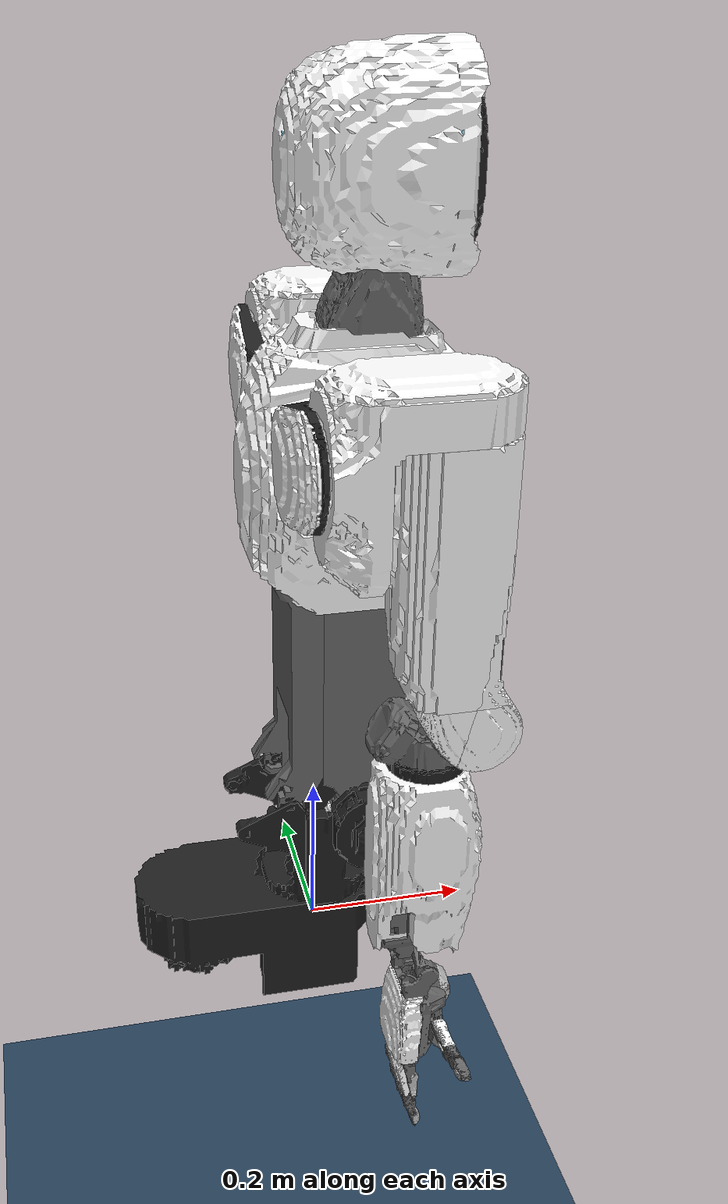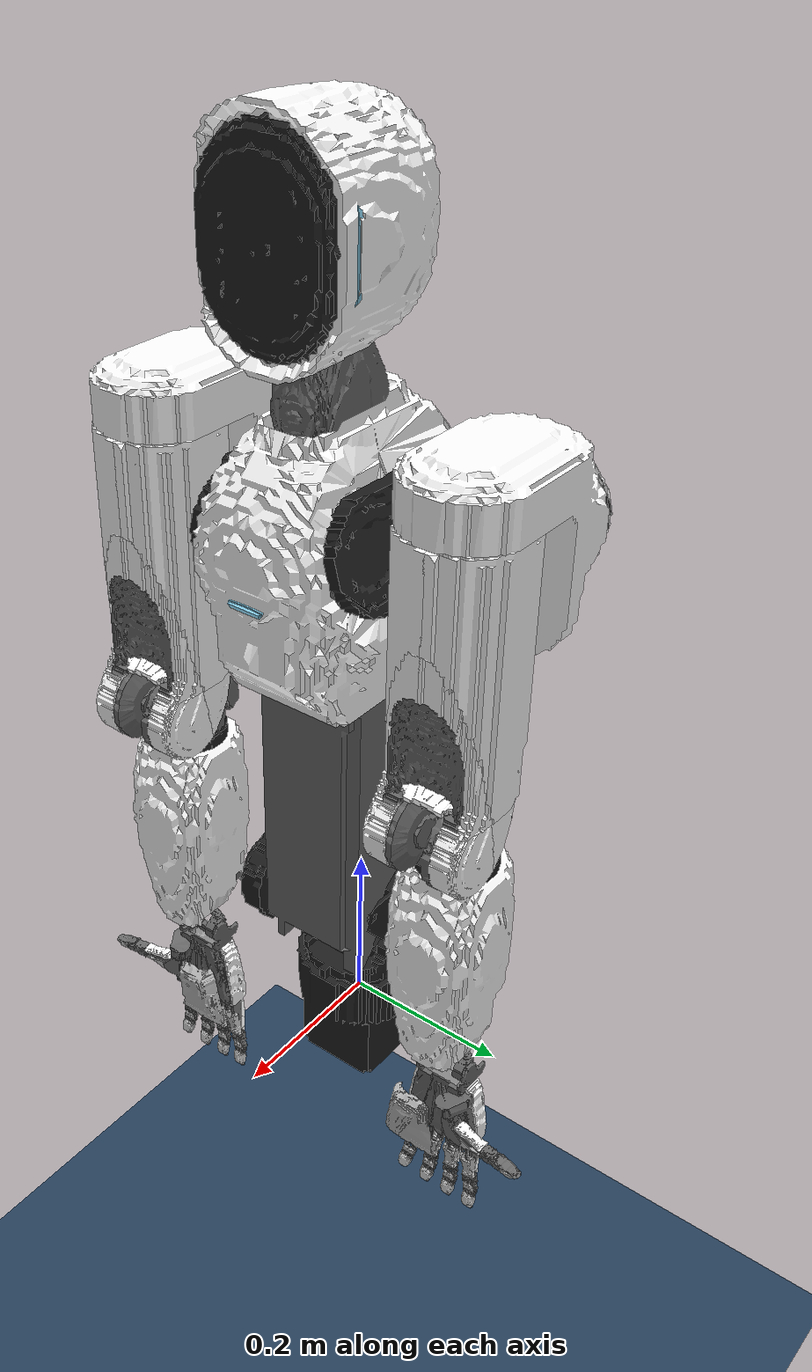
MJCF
<mujoco model="ALLEX scene">
  <include file="ALLEX.xml"/>
  <statistic center="0.031632 0.00125935 0.472039" extent="1.36164"/>
  <visual>
    <headlight diffuse="0.6 0.6 0.6" ambient="0.3 0.3 0.3" specular="0 0 0"/>
    <rgba haze="0.15 0.25 0.35 1"/>
    <global azimuth="120" elevation="-20"/>
  </visual>

  <asset>
    <texture type="skybox" builtin="gradient" rgb1="0.3 0.5 0.7" rgb2="0 0 0" width="512" height="3072"/>
    <texture type="2d" name="groundplane" builtin="checker" mark="edge" rgb1="0.2 0.3 0.4" rgb2="0.1 0.2 0.3"
      markrgb="0.8 0.8 0.8" width="300" height="300"/>
    <material name="groundplane" texture="groundplane" texuniform="true" texrepeat="5 5" reflectance="0.2"/>
  </asset>

  <worldbody>
    <light pos="0 0 3" dir="0 0 -1" directional="true"/>
    <!-- floor at fixed-mount ground level: base_to_ground=0.685 m below Base_Link -->
    <geom name="floor" pos="0 0 -0.685" size="0 0 0.05" type="plane" material="groundplane"/>
  </worldbody>
</mujoco>

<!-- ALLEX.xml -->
<mujoco model="ALLEX">
  <!-- ALLEX model_version 0.4.0 (proto-v4) — generated from internal SSoT; do not edit by hand. -->
  <!-- Compiler settings -->
  <compiler angle="radian" autolimits="true" meshdir="../meshes" />
  <option timestep="0.002" integrator="implicitfast" />

  <!-- Default setting -->
  <default>
    <default class="visual">
      <geom group="2" type="mesh" contype="0" conaffinity="0"/>
    </default>
    <default class="collision">
      <geom group="3" type="mesh"/>
    </default>
  </default>

  <asset>
    <!-- Material -->
    <material name="white" rgba="0.98 0.98 0.98 1"/>
    <material name="black" rgba="0.12 0.12 0.12 1"/>
    <material name="gray" rgba="0.4 0.4 0.4 1"/>
    <material name="pad" rgba="0.7 0.7 0.7 1"/>
    <material name="skyblue" rgba="0.53 0.81 0.92 1"/>

    <!-- Visual (geom class="visual" only) -->
    <mesh name="Base_Black" scale="0.001 0.001 0.001" file="Base_Black.stl"></mesh>
    <mesh name="Waist_Pitch_Back_Gray" scale="0.001 0.001 0.001" file="Waist_Pitch_Back_Gray.stl"></mesh>
    <mesh name="Waist_Pitch_Front_Gray" scale="0.001 0.001 0.001" file="Waist_Pitch_Front_Gray.stl"></mesh>
    <mesh name="Waist_Yaw_Black" scale="0.001 0.001 0.001" file="Waist_Yaw_Black.stl"></mesh>
    <mesh name="Chest_White" scale="0.001 0.001 0.001" file="Chest_White.stl"></mesh>
    <mesh name="Chest_Led" scale="0.001 0.001 0.001" file="Chest_Led.stl"></mesh>
    <mesh name="Neck_Pitch_Gray" scale="0.001 0.001 0.001" file="Neck_Pitch_Gray.stl"></mesh>
    <mesh name="Neck_Yaw_Face" scale="0.001 0.001 0.001" file="Neck_Yaw_Face.stl"></mesh>
    <mesh name="Neck_Yaw_Head" scale="0.001 0.001 0.001" file="Neck_Yaw_Head.stl"></mesh>
    <mesh name="Neck_Yaw_Cam" scale="0.001 0.001 0.001" file="Neck_Yaw_Cam.stl"></mesh>
    <mesh name="Neck_Yaw_Led" scale="0.001 0.001 0.001" file="Neck_Yaw_Led.stl"></mesh>
    <mesh name="R_Shoulder_Pitch_Black" scale="0.001 0.001 0.001" file="R_Shoulder_Pitch_Black.stl"></mesh>
    <mesh name="R_Shoulder_Pitch_White" scale="0.001 0.001 0.001" file="R_Shoulder_Pitch_White.stl"></mesh>
    <mesh name="L_Shoulder_Pitch_Black" scale="0.001 0.001 0.001" file="L_Shoulder_Pitch_Black.stl"></mesh>
    <mesh name="L_Shoulder_Pitch_White" scale="0.001 0.001 0.001" file="L_Shoulder_Pitch_White.stl"></mesh>
    <mesh name="Shoulder_RollYaw_White" scale="0.001 0.001 0.001" file="Shoulder_RollYaw_White.stl"></mesh>
    <mesh name="Upper_Arm_Gray" scale="0.001 0.001 0.001" file="Upper_Arm_Gray.stl"></mesh>
    <mesh name="Upper_Arm_White1" scale="0.001 0.001 0.001" file="Upper_Arm_White1.stl"></mesh>
    <mesh name="Upper_Arm_White2" scale="0.001 0.001 0.001" file="Upper_Arm_White2.stl"></mesh>
    <mesh name="Upper_Arm_White3" scale="0.001 0.001 0.001" file="Upper_Arm_White3.stl"></mesh>
    <mesh name="Upper_Arm_White4" scale="0.001 0.001 0.001" file="Upper_Arm_White4.stl"></mesh>
    <mesh name="Upper_Arm_White5" scale="0.001 0.001 0.001" file="Upper_Arm_White5.stl"></mesh>
    <mesh name="Upper_Arm_White6" scale="0.001 0.001 0.001" file="Upper_Arm_White6.stl"></mesh>
    <mesh name="Upper_Arm_White7" scale="0.001 0.001 0.001" file="Upper_Arm_White7.stl"></mesh>
    <mesh name="Upper_Arm_White8" scale="0.001 0.001 0.001" file="Upper_Arm_White8.stl"></mesh>
    <mesh name="Upper_Arm_White9" scale="0.001 0.001 0.001" file="Upper_Arm_White9.stl"></mesh>
    <mesh name="Elbow_Gray" scale="0.001 0.001 0.001" file="Elbow_Gray.stl"></mesh>
    <mesh name="Forearm_Black" scale="0.001 0.001 0.001" file="Forearm_Black.stl"></mesh>
    <mesh name="Forearm_Gray" scale="0.001 0.001 0.001" file="Forearm_Gray.stl"></mesh>
    <mesh name="Forearm_White" scale="0.001 0.001 0.001" file="Forearm_White.stl"></mesh>
    <mesh name="Wrist_Pitch_Gray" scale="0.001 0.001 0.001" file="Wrist_Pitch_Gray.stl"></mesh>
    <mesh name="Wrist_Roll_Gray" scale="0.001 0.001 0.001" file="Wrist_Roll_Gray.stl"></mesh>
    <mesh name="L_Palm_Gray" scale="0.001 0.001 0.001" file="L_Palm_Gray.stl"></mesh>
    <mesh name="L_Palm_Pad" scale="0.001 0.001 0.001" file="L_Palm_Pad.stl"></mesh>
    <mesh name="L_Palm_White" scale="0.001 0.001 0.001" file="L_Palm_White.stl"></mesh>
    <mesh name="L_Thumb_Distal_Gray" scale="0.001 0.001 0.001" file="L_Thumb_Distal_Gray.stl"></mesh>
    <mesh name="L_Thumb_Distal_Pad" scale="0.001 0.001 0.001" file="L_Thumb_Distal_Pad.stl"></mesh>
    <mesh name="L_Thumb_Middle_Gray" scale="0.001 0.001 0.001" file="L_Thumb_Middle_Gray.stl"></mesh>
    <mesh name="L_Thumb_Middle_Pad" scale="0.001 0.001 0.001" file="L_Thumb_Middle_Pad.stl"></mesh>
    <mesh name="L_Thumb_Proximal_Gray" scale="0.001 0.001 0.001" file="L_Thumb_Proximal_Gray.stl"></mesh>
    <mesh name="L_Thumb_Proximal_Pad" scale="0.001 0.001 0.001" file="L_Thumb_Proximal_Pad.stl"></mesh>
    <mesh name="L_Thumb_Proximal_White" scale="0.001 0.001 0.001" file="L_Thumb_Proximal_White.stl"></mesh>
    <mesh name="L_Thumb_Yaw_Gray" scale="0.001 0.001 0.001" file="L_Thumb_Yaw_Gray.stl"></mesh>
    <mesh name="R_Palm_Gray" scale="0.001 0.001 0.001" file="R_Palm_Gray.stl"></mesh>
    <mesh name="R_Palm_Pad" scale="0.001 0.001 0.001" file="R_Palm_Pad.stl"></mesh>
    <mesh name="R_Palm_White" scale="0.001 0.001 0.001" file="R_Palm_White.stl"></mesh>
    <mesh name="R_Thumb_Distal_Gray" scale="0.001 0.001 0.001" file="R_Thumb_Distal_Gray.stl"></mesh>
    <mesh name="R_Thumb_Distal_Pad" scale="0.001 0.001 0.001" file="R_Thumb_Distal_Pad.stl"></mesh>
    <mesh name="R_Thumb_Middle_Gray" scale="0.001 0.001 0.001" file="R_Thumb_Middle_Gray.stl"></mesh>
    <mesh name="R_Thumb_Middle_Pad" scale="0.001 0.001 0.001" file="R_Thumb_Middle_Pad.stl"></mesh>
    <mesh name="R_Thumb_Proximal_Gray" scale="0.001 0.001 0.001" file="R_Thumb_Proximal_Gray.stl"></mesh>
    <mesh name="R_Thumb_Proximal_Pad" scale="0.001 0.001 0.001" file="R_Thumb_Proximal_Pad.stl"></mesh>
    <mesh name="R_Thumb_Proximal_White" scale="0.001 0.001 0.001" file="R_Thumb_Proximal_White.stl"></mesh>
    <mesh name="R_Thumb_Yaw_Gray" scale="0.001 0.001 0.001" file="R_Thumb_Yaw_Gray.stl"></mesh>
    <mesh name="Finger_Roll_Gray" scale="0.001 0.001 0.001" file="Finger_Roll_Gray.stl"></mesh>
    <mesh name="Finger_Distal_Gray" scale="0.001 0.001 0.001" file="Finger_Distal_Gray.stl"></mesh>
    <mesh name="Finger_Distal_Pad" scale="0.001 0.001 0.001" file="Finger_Distal_Pad.stl"></mesh>
    <mesh name="Finger_Middle_Gray" scale="0.001 0.001 0.001" file="Finger_Middle_Gray.stl"></mesh>
    <mesh name="Finger_Middle_Pad" scale="0.001 0.001 0.001" file="Finger_Middle_Pad.stl"></mesh>
    <mesh name="Finger_Proximal_Gray" scale="0.001 0.001 0.001" file="Finger_Proximal_Gray.stl"></mesh>
    <mesh name="Finger_Proximal_Pad" scale="0.001 0.001 0.001" file="Finger_Proximal_Pad.stl"></mesh>
    <mesh name="Finger_Proximal_White" scale="0.001 0.001 0.001" file="Finger_Proximal_White.stl"></mesh>

    <!-- Collision (geom class="collision" only) -->
    <mesh name="Base_Collision" scale="0.001 0.001 0.001" file="Base_Collision.stl"></mesh>
    <mesh name="Waist_Pitch_Front_Collision" scale="0.001 0.001 0.001" file="Waist_Pitch_Front_Collision.stl"></mesh>
    <mesh name="Waist_Yaw_Collision" scale="0.001 0.001 0.001" file="Waist_Yaw_Collision.stl"></mesh>
    <mesh name="Chest_Collision" scale="0.001 0.001 0.001" file="Chest_Collision.stl"></mesh>
    <mesh name="Neck_Pitch_Collision" scale="0.001 0.001 0.001" file="Neck_Pitch_Collision.stl"></mesh>
    <mesh name="Neck_Yaw_Collision" scale="0.001 0.001 0.001" file="Neck_Yaw_Collision.stl"></mesh>
    <mesh name="L_Shoulder_Pitch_Collision1" scale="0.001 0.001 0.001" file="L_Shoulder_Pitch_Collision1.stl"></mesh>
    <mesh name="L_Shoulder_Pitch_Collision2" scale="0.001 0.001 0.001" file="L_Shoulder_Pitch_Collision2.stl"></mesh>
    <mesh name="L_Shoulder_Pitch_Collision3" scale="0.001 0.001 0.001" file="L_Shoulder_Pitch_Collision3.stl"></mesh>
    <mesh name="R_Shoulder_Pitch_Collision1" scale="0.001 0.001 0.001" file="R_Shoulder_Pitch_Collision1.stl"></mesh>
    <mesh name="R_Shoulder_Pitch_Collision2" scale="0.001 0.001 0.001" file="R_Shoulder_Pitch_Collision2.stl"></mesh>
    <mesh name="R_Shoulder_Pitch_Collision3" scale="0.001 0.001 0.001" file="R_Shoulder_Pitch_Collision3.stl"></mesh>
    <mesh name="Shoulder_RollYaw_Collision1" scale="0.001 0.001 0.001" file="Shoulder_RollYaw_Collision1.stl"></mesh>
    <mesh name="Shoulder_RollYaw_Collision2" scale="0.001 0.001 0.001" file="Shoulder_RollYaw_Collision2.stl"></mesh>
    <mesh name="Upper_Arm_Collision1" scale="0.001 0.001 0.001" file="Upper_Arm_Collision1.stl"></mesh>
    <mesh name="Upper_Arm_Collision2" scale="0.001 0.001 0.001" file="Upper_Arm_Collision2.stl"></mesh>
    <mesh name="Upper_Arm_Collision3" scale="0.001 0.001 0.001" file="Upper_Arm_Collision3.stl"></mesh>
    <mesh name="Elbow_Collision" scale="0.001 0.001 0.001" file="Elbow_Collision.stl"></mesh>
    <mesh name="Forearm_Collision1" scale="0.001 0.001 0.001" file="Forearm_Collision1.stl"></mesh>
    <mesh name="Forearm_Collision2" scale="0.001 0.001 0.001" file="Forearm_Collision2.stl"></mesh>
    <mesh name="Forearm_Collision3" scale="0.001 0.001 0.001" file="Forearm_Collision3.stl"></mesh>
    <mesh name="Wrist_Pitch_Collision1" scale="0.001 0.001 0.001" file="Wrist_Pitch_Collision1.stl"></mesh>
    <mesh name="Wrist_Pitch_Collision2" scale="0.001 0.001 0.001" file="Wrist_Pitch_Collision2.stl"></mesh>
    <mesh name="Wrist_Pitch_Collision3" scale="0.001 0.001 0.001" file="Wrist_Pitch_Collision3.stl"></mesh>
    <mesh name="Wrist_Roll_Collision" scale="0.001 0.001 0.001" file="Wrist_Roll_Collision.stl"></mesh>
    <mesh name="L_Thumb_Distal_Collision" scale="0.001 0.001 0.001" file="L_Thumb_Distal_Collision.stl"></mesh>
    <mesh name="L_Thumb_Distal_Collision2" scale="0.001 0.001 0.001" file="L_Thumb_Distal_Collision2.stl"></mesh>
    <mesh name="L_Thumb_Middle_Collision" scale="0.001 0.001 0.001" file="L_Thumb_Middle_Collision.stl"></mesh>
    <mesh name="L_Thumb_Proximal_Collision" scale="0.001 0.001 0.001" file="L_Thumb_Proximal_Collision.stl"></mesh>
    <mesh name="L_Thumb_Yaw_Collision" scale="0.001 0.001 0.001" file="L_Thumb_Yaw_Collision.stl"></mesh>
    <mesh name="L_Palm_Back_Collision1" scale="0.001 0.001 0.001" file="L_Palm_Back_Collision1.stl"></mesh>
    <mesh name="L_Palm_Back_Collision2" scale="0.001 0.001 0.001" file="L_Palm_Back_Collision2.stl"></mesh>
    <mesh name="L_Palm_Back_Collision3" scale="0.001 0.001 0.001" file="L_Palm_Back_Collision3.stl"></mesh>
    <mesh name="L_Palm_Frame_Collision1" scale="0.001 0.001 0.001" file="L_Palm_Frame_Collision1.stl"></mesh>
    <mesh name="L_Palm_Frame_Collision2" scale="0.001 0.001 0.001" file="L_Palm_Frame_Collision2.stl"></mesh>
    <mesh name="L_Palm_Frame_Collision3" scale="0.001 0.001 0.001" file="L_Palm_Frame_Collision3.stl"></mesh>
    <mesh name="L_Palm_Frame_Collision4" scale="0.001 0.001 0.001" file="L_Palm_Frame_Collision4.stl"></mesh>
    <mesh name="L_Palm_Frame_Collision5" scale="0.001 0.001 0.001" file="L_Palm_Frame_Collision5.stl"></mesh>
    <mesh name="L_Palm_Frame_Collision6" scale="0.001 0.001 0.001" file="L_Palm_Frame_Collision6.stl"></mesh>
    <mesh name="L_Palm_Frame_Collision7" scale="0.001 0.001 0.001" file="L_Palm_Frame_Collision7.stl"></mesh>
    <mesh name="L_Palm_Pad_Collision1" scale="0.001 0.001 0.001" file="L_Palm_Pad_Collision1.stl"></mesh>
    <mesh name="L_Palm_Pad_Collision2" scale="0.001 0.001 0.001" file="L_Palm_Pad_Collision2.stl"></mesh>
    <mesh name="L_Palm_Pad_Collision3" scale="0.001 0.001 0.001" file="L_Palm_Pad_Collision3.stl"></mesh>
    <mesh name="R_Palm_Back_Collision1" scale="0.001 0.001 0.001" file="R_Palm_Back_Collision1.stl"></mesh>
    <mesh name="R_Palm_Back_Collision2" scale="0.001 0.001 0.001" file="R_Palm_Back_Collision2.stl"></mesh>
    <mesh name="R_Palm_Back_Collision3" scale="0.001 0.001 0.001" file="R_Palm_Back_Collision3.stl"></mesh>
    <mesh name="R_Palm_Frame_Collision1" scale="0.001 0.001 0.001" file="R_Palm_Frame_Collision1.stl"></mesh>
    <mesh name="R_Palm_Frame_Collision2" scale="0.001 0.001 0.001" file="R_Palm_Frame_Collision2.stl"></mesh>
    <mesh name="R_Palm_Frame_Collision3" scale="0.001 0.001 0.001" file="R_Palm_Frame_Collision3.stl"></mesh>
    <mesh name="R_Palm_Frame_Collision4" scale="0.001 0.001 0.001" file="R_Palm_Frame_Collision4.stl"></mesh>
    <mesh name="R_Palm_Frame_Collision5" scale="0.001 0.001 0.001" file="R_Palm_Frame_Collision5.stl"></mesh>
    <mesh name="R_Palm_Frame_Collision6" scale="0.001 0.001 0.001" file="R_Palm_Frame_Collision6.stl"></mesh>
    <mesh name="R_Palm_Frame_Collision7" scale="0.001 0.001 0.001" file="R_Palm_Frame_Collision7.stl"></mesh>
    <mesh name="R_Palm_Pad_Collision1" scale="0.001 0.001 0.001" file="R_Palm_Pad_Collision1.stl"></mesh>
    <mesh name="R_Palm_Pad_Collision2" scale="0.001 0.001 0.001" file="R_Palm_Pad_Collision2.stl"></mesh>
    <mesh name="R_Palm_Pad_Collision3" scale="0.001 0.001 0.001" file="R_Palm_Pad_Collision3.stl"></mesh>
    <mesh name="R_Thumb_Distal_Collision" scale="0.001 0.001 0.001" file="R_Thumb_Distal_Collision.stl"></mesh>
    <mesh name="R_Thumb_Distal_Collision2" scale="0.001 0.001 0.001" file="R_Thumb_Distal_Collision2.stl"></mesh>
    <mesh name="R_Thumb_Middle_Collision" scale="0.001 0.001 0.001" file="R_Thumb_Middle_Collision.stl"></mesh>
    <mesh name="R_Thumb_Proximal_Collision" scale="0.001 0.001 0.001" file="R_Thumb_Proximal_Collision.stl"></mesh>
    <mesh name="R_Thumb_Yaw_Collision" scale="0.001 0.001 0.001" file="R_Thumb_Yaw_Collision.stl"></mesh>
    <mesh name="Finger_Roll_Collision" scale="0.001 0.001 0.001" file="Finger_Roll_Collision.stl"></mesh>
    <mesh name="Finger_Distal_Collision" scale="0.001 0.001 0.001" file="Finger_Distal_Collision.stl"></mesh>
    <mesh name="Finger_Distal_Collision2" scale="0.001 0.001 0.001" file="Finger_Distal_Collision2.stl"></mesh>
    <mesh name="Finger_Middle_Collision" scale="0.001 0.001 0.001" file="Finger_Middle_Collision.stl"></mesh>
    <mesh name="Finger_Proximal_Collision" scale="0.001 0.001 0.001" file="Finger_Proximal_Collision.stl"></mesh>
  </asset>

  <worldbody>
    <body name="Base_Link" pos="0 0 0">
      <inertial pos="0 0 0" mass="3.0" diaginertia="0.001 0.001 0.001"/>
      <geom class="collision" mesh="Base_Collision"/>
      <geom class="visual" material="black" mesh="Base_Black"/>

      <body name="Waist_Yaw_Link" pos="0 0 0.064">
        <inertial pos="0.011694814 -0.023786125 0.046361293" mass="3.62644339" quat="0.3974000916 -0.1459264551 0.197839197 0.8841030986" diaginertia="0.03131222484 0.02196348128 0.01267129388"/>
        <joint name="Waist_Yaw_Joint" axis="0 0 1" range="-2.8797933 2.8797933" frictionloss="4.361" damping="0.95" armature="0.088606" actuatorfrcrange="-130 130" />
        <geom class="collision" mesh="Waist_Yaw_Collision"/>
        <geom class="visual" material="black" mesh="Waist_Yaw_Black"/>

        <body name="Waist_Pitch_Back_Link" pos="-0.04 0 0.15">
          <inertial pos="0.020387801 0.000182755 0.158712024" mass="0.9409332" quat="0.9999760493 -0.001350538461 0.006700826559 0.001084320401" diaginertia="0.01218475116 0.01019404767 0.002481201169"/>
          <joint name="Waist_Pitch_Dummy_Joint" axis="0 1 0" range="-0.5235988 1.0471976" />
          <geom class="visual" material="gray" mesh="Waist_Pitch_Back_Gray"/>
        </body>

        <body name="Waist_Lower_Pitch_Link" pos="0.06 0 0.12">
          <inertial pos="-0.029734297 0.002246639 0.109363279" mass="5.75979036" quat="0.7276632348 -0.04178699705 -0.04676344654 0.683061669" diaginertia="0.1077437518 0.09954180492 0.02037344325"/>
          <joint name="Waist_Lower_Pitch_Joint" axis="0 1 0" range="-0.5235988 1.0471976" frictionloss="2.31675" damping="0.01" armature="0.021048" actuatorfrcrange="-152 152" />
          <geom class="collision" mesh="Waist_Pitch_Front_Collision"/>
          <geom class="visual" material="gray" mesh="Waist_Pitch_Front_Gray"/>

          <body name="Waist_Upper_Pitch_Link" pos="0 0 0.32">
            <inertial pos="-0.0397 -0.0003 0.1189" mass="2.780295" quat="0.574755169438 0.5776966558257 0.4098145677849 -0.4098476413051" diaginertia="0.01851936771171 0.02078400479409 0.02753238135412"/>
            <joint name="Waist_Upper_Pitch_Joint" axis="0 1 0" range="-1.0471976 0.5235988" />
            <geom class="collision" mesh="Chest_Collision"/>
            <geom class="visual" material="skyblue" mesh="Chest_Led"/>
            <geom class="visual" material="white" mesh="Chest_White"/>

            <body name="Chest_Origin_Link" pos="0.0415 0 0.149">
              <inertial pos="0 0 0" mass="0" diaginertia="0.001 0.001 0.001"/>

              <body name="Neck_Pitch_Link" pos="-0.0335 0 0.1380804">
                <inertial pos="-0.014276891 -0.005693118 0.046971122" mass="0.370429008" quat="0.703362819 0.1012479509 0.01932232739 0.7033180255" diaginertia="0.001033179321 0.0009813730878 0.0003424475908"/>
                <joint name="Neck_Pitch_Joint" axis="0 1 0" range="-0.6981317 0.8726646" frictionloss="0.33968" damping="0.0" armature="0.004" actuatorfrcrange="-12 12" />
                <geom class="collision" mesh="Neck_Pitch_Collision"/>
                <geom class="visual" material="gray" mesh="Neck_Pitch_Gray"/>

                <body name="Neck_Yaw_Link" pos="-0.0000005 0 0.093">
                  <inertial pos="0.032970912 0.000181574 0.052561074" mass="1.884994309" quat="0.9907821549 -0.01440713929 -0.1091037513 0.07899067856" diaginertia="0.007435779579 0.007303827358 0.005808393062"/>
                  <joint name="Neck_Yaw_Joint" axis="0 0 1" range="-1.570796 1.570796" frictionloss="0.1501" damping="0.0" armature="0.006" actuatorfrcrange="-6 6" />
                  <geom class="collision" mesh="Neck_Yaw_Collision"/>
                  <geom class="visual" material="black" mesh="Neck_Yaw_Face"/>
                  <geom class="visual" material="white" mesh="Neck_Yaw_Head"/>
                  <geom class="visual" material="black" mesh="Neck_Yaw_Cam"/>
                  <geom class="visual" material="skyblue" mesh="Neck_Yaw_Led"/>

                  <!-- RealSense D435i: RGB 69°×42°, depth 87°×58°, ideal range 0.3–3 m -->
                  <body name="realsense_link" pos="0.0753 0 0.1029">
                    <camera name="realsense_color_optical_frame" pos="0.011 0.033 0.013" quat="-0.5 -0.5 0.5 0.5" fovy="42" />
                    <camera name="realsense_depth_optical_frame" pos="0.011 0.018 0.013" quat="-0.5 -0.5 0.5 0.5" fovy="58" />
                  </body>

                  <!-- Orbbec Femto Bolt: RGB 80°×51°, depth 120°×120°(WFOV)/75°×65°(NFOV), ideal range 0.25–5.46 m -->
                  <body name="orbbec_link" pos="0.0893 0.002 0.0733">
                    <camera name="orbbec_color_optical_frame" pos="-0.002 -0.033 -0.001" quat="-0.5 -0.5 0.5 0.5" fovy="51" />
                    <camera name="orbbec_depth_optical_frame" pos="0 0 0" quat="-0.5 -0.5 0.5 0.5" fovy="120"/>
                  </body>

                  <!-- ZED Mini: RGB 102°×57°, ideal range 0.1–9 m -->
                  <body name="zed_camera_link" pos="0.067225 0 0.0145">
                    <camera name="zed_left_camera_optical_frame" pos="0.000 0.032 0.013" quat="-0.5 -0.5 0.5 0.5" fovy="57" />
                  </body>
                </body>
              </body>

              <body name="L_Shoulder_Pitch_Link" pos="0 0.0710988 0.0190509" quat="0.9914449 0.1305262 2e-7 0.0000013">
                <inertial pos="-0.0900 0.0375  -0.0007" mass="1.015421884" quat="0.3367978603 0.4015577255 0.5765591148 0.6268159071" diaginertia="0.007933697221 0.007335840776 0.002641462003"/>
                <joint name="L_Shoulder_Pitch_Joint" axis="0 1 0" range="-3.316126 1.745329" armature="0.050390311" frictionloss="1" damping="0" actuatorfrcrange="-120 120" actuatorgravcomp="true" />
                <geom class="collision" mesh="L_Shoulder_Pitch_Collision1"/>
                <geom class="collision" mesh="L_Shoulder_Pitch_Collision2"/>
                <geom class="collision" mesh="L_Shoulder_Pitch_Collision3"/>
                <geom class="visual" material="black" mesh="L_Shoulder_Pitch_Black"/>
                <geom class="visual" material="white" mesh="L_Shoulder_Pitch_White"/>

                <body name="L_Shoulder_RollYaw_Link" pos="-0.1365 0.1195 0" quat="0.9914449 -0.1305262 -2e-7 0.0000013">
                  <inertial pos="0.0678  0.0001  0.0400" mass="2.869014517" quat="0.6517571384 -0.2372772909 -0.2274677093 0.6834987645" diaginertia="0.01640162022 0.0152242395 0.006928140276"/>
                  <joint name="L_Shoulder_Roll_Joint" axis="1 0 0" range="-0.087266 3.752458" armature="0.050390311" frictionloss="2.5" damping="0" actuatorfrcrange="-120 120" actuatorgravcomp="true" />
                  <geom class="collision" mesh="Shoulder_RollYaw_Collision1"/>
                  <geom class="collision" mesh="Shoulder_RollYaw_Collision2"/>
                  <geom class="visual" material="white" mesh="Shoulder_RollYaw_White"/>

                  <body name="L_Upper_Arm_Link" pos="0.1365 0 0.0315">
                    <inertial pos="0.0013  0.0003  -0.1955" quat="0.6928881439341 -0.01123129209145 0.7209187267705 0.007487821119587" mass="3.51" diaginertia="0.006281650 0.029898693 0.030695144" />
                    <joint name="L_Shoulder_Yaw_Joint" axis="0 0 1" range="-3.316126 1.745329" armature="0.050390311" frictionloss="1" damping="0" actuatorfrcrange="-120 120" actuatorgravcomp="true" />
                    <geom class="collision" mesh="Upper_Arm_Collision1"/>
                    <geom class="collision" mesh="Upper_Arm_Collision2"/>
                    <geom class="collision" mesh="Upper_Arm_Collision3"/>
                    <geom class="visual" material="gray" mesh="Upper_Arm_Gray"/>
                    <geom class="visual" material="white" mesh="Upper_Arm_White1"/>
                    <geom class="visual" material="white" mesh="Upper_Arm_White2"/>
                    <geom class="visual" material="white" mesh="Upper_Arm_White3"/>
                    <geom class="visual" material="white" mesh="Upper_Arm_White4"/>
                    <geom class="visual" material="white" mesh="Upper_Arm_White5"/>
                    <geom class="visual" material="white" mesh="Upper_Arm_White6"/>
                    <geom class="visual" material="white" mesh="Upper_Arm_White7"/>
                    <geom class="visual" material="white" mesh="Upper_Arm_White8"/>
                    <geom class="visual" material="white" mesh="Upper_Arm_White9"/>

                    <body name="L_Elbow_Link" pos="0.03 0 -0.3255">
                      <inertial pos="-0.0231 0.00005 -0.0086" quat="0.9923469986915 -0.03256696117952 0.1190500913747 0.003728668831823" mass="0.784434687" diaginertia="0.0007918289688995 0.001534644638612 0.001826444338174" />
                      <joint name="L_Elbow_Joint" axis="0 1 0" range="-2.792527 0.087266" armature="0.022888756" frictionloss="1.5" damping="0" actuatorfrcrange="-100 100" actuatorgravcomp="true" />
                      <geom class="collision" mesh="Elbow_Collision"/>
                      <geom class="visual" material="gray" mesh="Elbow_Gray"/>

                      <body name="L_Forearm_Link" pos="-0.045 0 -0.045">
                        <inertial pos="-0.0079 -0.0001 -0.1425" quat="-0.5249016149751 0.5268096669399 0.4722701607646 0.4731921012301" mass="3.1" diaginertia="0.003917052543262 0.01588830836955 0.01689145229235" />
                        <joint name="L_Wrist_Yaw_Joint" axis="0 0 1" range="-4.799655 0.610865" armature="0.008184087" frictionloss="1" damping="0" actuatorfrcrange="-60 60" actuatorgravcomp="true" />
                        <geom class="collision" mesh="Forearm_Collision1"/>
                        <geom class="collision" mesh="Forearm_Collision2"/>
                        <geom class="collision" mesh="Forearm_Collision3"/>
                        <geom class="visual" material="black" mesh="Forearm_Black"/>
                        <geom class="visual" material="gray" mesh="Forearm_Gray"/>
                        <geom class="visual" material="white" mesh="Forearm_White"/>

                        <body name="L_Wrist_Roll_Link" pos="-0.0085 0 -0.2725">
                          <inertial pos="-0.0004 0.0003 -0.0230" mass="0.172" quat="0.6515269405 0.6915297445 0.2482436165 -0.1888765872" diaginertia="4.659727589e-05 3.368803397e-05 1.771469014e-05"/>
                          <joint name="L_Wrist_Roll_Joint" axis="1 0 0" range="-0.872665 0.872665" armature="0.001750703" frictionloss="0.3" damping="0" actuatorfrcrange="-20 20" actuatorgravcomp="true" />
                          <geom class="collision" mesh="Wrist_Roll_Collision"/>
                          <geom class="visual" material="gray" mesh="Wrist_Roll_Gray"/>

                          <body name="L_Wrist_Pitch_Link" pos="0.0135 0 -0.025">
                            <inertial pos="-0.0115 -0.0061 -0.1013" mass="0.97383" quat="0.9998356286 0.004005407735 0.0131161993 0.01185908277" diaginertia="0.001751025141 0.00137983739 0.0005701374694"/>
                            <joint name="L_Wrist_Pitch_Joint" axis="0 1 0" range="-1.396263 1.396263" armature="0.001392972" frictionloss="0.3" damping="0" actuatorfrcrange="-18 18" actuatorgravcomp="true" />
                            <geom class="collision" mesh="Wrist_Pitch_Collision1"/>
                            <geom class="collision" mesh="Wrist_Pitch_Collision2"/>
                            <geom class="collision" mesh="Wrist_Pitch_Collision3"/>
                            <geom class="visual" material="gray" mesh="Wrist_Pitch_Gray"/>

                            <body name="L_Palm_Link" pos="0.0045 0 -0.095">
                            <inertial pos="0 0 0" mass="0" diaginertia="0.001 0.001 0.001"/>
                            <geom class="collision" mesh="L_Palm_Back_Collision1"/>
                            <geom class="collision" mesh="L_Palm_Back_Collision2"/>
                            <geom class="collision" mesh="L_Palm_Back_Collision3"/>
                            <geom class="collision" mesh="L_Palm_Frame_Collision1"/>
                            <geom class="collision" mesh="L_Palm_Frame_Collision2"/>
                            <geom class="collision" mesh="L_Palm_Frame_Collision3"/>
                            <geom class="collision" mesh="L_Palm_Frame_Collision4"/>
                            <geom class="collision" mesh="L_Palm_Frame_Collision5"/>
                            <geom class="collision" mesh="L_Palm_Frame_Collision6"/>
                            <geom class="collision" mesh="L_Palm_Frame_Collision7"/>
                            <geom class="collision" mesh="L_Palm_Pad_Collision1"/>
                            <geom class="collision" mesh="L_Palm_Pad_Collision2"/>
                            <geom class="collision" mesh="L_Palm_Pad_Collision3"/>
                            <geom class="visual" material="gray" mesh="L_Palm_Gray"/>
                            <geom class="visual" material="pad" mesh="L_Palm_Pad"/>
                            <geom class="visual" material="white" mesh="L_Palm_White"/>

                              <body name="L_Thumb_Yaw_Link" pos="0.0098274 0.0210533 0.0360908" quat="0.9948891 0.0466857 0.0607223 -0.0657952">
                                <inertial pos="-0.000007001 0.002747764 -0.019328997" mass="0.032789432" quat="0.6889635765 0.1034706852 -0.1095633224 0.7089561946" diaginertia="1.047862936e-05 1.044061826e-05 1.500975652e-06"/>
                                <joint name="L_Thumb_Yaw_Joint" axis="0 0 -1" range="0 2.617994" armature="0.00801347" frictionloss="0.03874" damping="0" actuatorfrcrange="-1.5 1.5" />
                                <geom class="collision" mesh="L_Thumb_Yaw_Collision"/>
                                <geom class="visual" material="gray" mesh="L_Thumb_Yaw_Gray"/>

                                <body name="L_Thumb_Proximal_Link" pos="0 0.0139985 -0.0323434">
                                  <inertial pos="-0.0000454521 0.0190620346 0.0080043456" mass="0.030992843" quat="0.50466803 0.49355209 -0.50597526 -0.49568695" diaginertia="2.32456382e-06 4.93604313e-06 6.12243002e-06"/>
                                  <joint name="L_Thumb_CMC_Joint" axis="-1 0 0" range="0 1.570796" armature="0.00339975" frictionloss="0.05879" damping="0" actuatorfrcrange="-4.5 4.5" />
                                  <geom class="collision" mesh="L_Thumb_Proximal_Collision" contype="2" conaffinity="4"/>
                                  <geom class="visual" material="gray" mesh="L_Thumb_Proximal_Gray"/>
                                  <geom class="visual" material="pad" mesh="L_Thumb_Proximal_Pad"/>
                                  <geom class="visual" material="white" mesh="L_Thumb_Proximal_White"/>

                                  <body name="L_Thumb_Middle_Link" pos="0 0.04399902 0.00029399">
                                    <inertial pos="0.000002618821 0.006468415814 0.002006469640" mass="0.007144084" quat="0.70638504 -0.03394324 0.0396098 0.70590303" diaginertia="2.44419393e-07 4.43004550e-07 4.54987785e-07"/>
                                    <joint name="L_Thumb_MCP_Joint" axis="-1 0 0" range="0 1.570796" armature="0.00154476" frictionloss="0.01850" damping="0" actuatorfrcrange="-3 3" />
                                    <geom class="collision" mesh="L_Thumb_Middle_Collision"/>
                                    <geom class="visual" material="gray" mesh="L_Thumb_Middle_Gray"/>
                                    <geom class="visual" material="pad" mesh="L_Thumb_Middle_Pad"/>

                                    <body name="L_Thumb_Distal_Link" pos="0 0.019 0">
                                      <inertial pos="0.000003439 0.005724653 0.002653430" mass="0.00504" quat="0.4993579122 0.5024384358 -0.5010644362 0.4971234499" diaginertia="3.653666766e-07 3.440241684e-07 1.050724157e-07"/>
                                      <joint name="L_Thumb_IP_Joint" axis="-1 0 0" frictionloss="0" damping="0" />
                                      <geom class="collision" mesh="L_Thumb_Distal_Collision" rgba="1 1 1 1"/>
                                      <geom class="visual" material="gray" mesh="L_Thumb_Distal_Gray"/>
                                      <body name="L_Thumb_Fingertip" pos="0 0.00834238 -0.00823029" quat="0.99306846 -0.1175374 0 0">
                                        <geom class="collision" mesh="L_Thumb_Distal_Collision2" rgba="1 1 0 1"/>
                                        <geom class="visual" material="pad" mesh="L_Thumb_Distal_Pad"/>
                                      </body>
                                    </body>
                                  </body>
                                </body>
                              </body>

                              <body name="L_Index_Roll_Link" pos="-0.0186259 0.0330567 -0.0383928" quat="0.983335 0.0474832 -0.172299 -0.0333266">
                                <inertial pos="-0.001315071 0.000324987 -0.001749841" mass="0.00611" quat="0.4086654509 0.3609801778 -0.6507565651 0.5283954518" diaginertia="1.979800835e-07 1.357177666e-07 1.024453156e-07"/>
                                <joint name="L_Index_ABAD_Joint" axis="1 0 0" range="-0.523599 0.523599" armature="1.53134E-04" frictionloss="0.01379956" damping="0" actuatorfrcrange="-3.5 3.5" />
                                <geom class="collision" mesh="Finger_Roll_Collision"/>
                                <geom class="visual" material="gray" mesh="Finger_Roll_Gray"/>

                                <body name="L_Index_Proximal_Link" pos="-0.003817 0 -0.0061246" quat="0.9848078 0 0.1736482 0">
                                  <inertial pos="-0.005831596 0.000042198 -0.019211920" mass="0.02387" quat="0.696735057 -0.06434181103 -0.06210385849 0.7117327465" diaginertia="6.642950653e-06 6.51700556e-06 8.852664619e-07"/>
                                  <joint name="L_Index_MCP_Joint" axis="0 -1 0" range="-0.174532 1.570796" armature="0.00388912" frictionloss="0.04563921" damping="0" actuatorfrcrange="-5 5" />
                                  <geom class="collision" mesh="Finger_Proximal_Collision"/>
                                  <geom class="visual" material="gray" mesh="Finger_Proximal_Gray"/>
                                  <geom class="visual" material="pad" mesh="Finger_Proximal_Pad"/>
                                  <geom class="visual" material="white" mesh="Finger_Proximal_White"/>

                                  <body name="L_Index_Middle_Link" pos="0 0 -0.052">
                                    <inertial pos="-0.001717810 0.000001917 -0.006013520" mass="0.00977" quat="0.998100897 0.0001897506431 0.06159687216 -0.0006235510703" diaginertia="7.395801064e-07 6.707525648e-07 3.192749713e-07"/>
                                    <joint name="L_Index_PIP_Joint" axis="0 -1 0" range="0 1.9198622" armature="0.00154476" frictionloss="0.02103825" damping="0" actuatorfrcrange="-3 3" />
                                    <geom class="collision" mesh="Finger_Middle_Collision"/>
                                    <geom class="visual" material="gray" mesh="Finger_Middle_Gray"/>
                                    <geom class="visual" material="pad" mesh="Finger_Middle_Pad"/>

                                    <body name="L_Index_Distal_Link" pos="0.0019932 0 -0.0188952">
                                      <inertial pos="-0.002635323 -0.000003528 -0.00600072" mass="0.00504" quat="0.9999814857 -0.0004422177879 0.005771251628 0.001877577352" diaginertia="3.488369153e-07 3.281665762e-07 1.037075906e-07"/>
                                      <joint name="L_Index_DIP_Joint" axis="0 -1 0" frictionloss="0" damping="0" />
                                      <geom class="collision" mesh="Finger_Distal_Collision" rgba="1 1 1 1"/>
                                      <geom class="visual" material="gray" mesh="Finger_Distal_Gray"/>
                                      <body name="L_Index_Fingertip" pos="0.0082309 0 -0.0083419" quat="0.9930646 0 -0.1175706 0">
                                        <geom class="collision" mesh="Finger_Distal_Collision2" rgba="1 1 0 1"/>
                                        <geom class="visual" material="pad" mesh="Finger_Distal_Pad"/>
                                      </body>
                                    </body>
                                  </body>
                                </body>
                              </body>

                              <body name="L_Middle_Roll_Link" pos="-0.0197378 0.0111686 -0.0403088" quat="0.9848078 0 -0.1736482 0">
                                <inertial pos="-0.001315071 0.000324987 -0.001749841" mass="0.00611" quat="0.4086654509 0.3609801778 -0.6507565651 0.5283954518" diaginertia="1.979800835e-07 1.357177666e-07 1.024453156e-07"/>
                                <joint name="L_Middle_ABAD_Joint" axis="1 0 0" range="-0.523599 0.523599" armature="1.53134E-04" frictionloss="0.01379956" damping="0" actuatorfrcrange="-3.5 3.5" />
                                <geom class="collision" mesh="Finger_Roll_Collision"/>
                                <geom class="visual" material="gray" mesh="Finger_Roll_Gray"/>

                                <body name="L_Middle_Proximal_Link" pos="-0.003817 0 -0.0061246" quat="0.9848078 0 0.1736482 0">
                                  <inertial pos="-0.005831596 0.000042198 -0.019211920" mass="0.02387" quat="0.696735057 -0.06434181103 -0.06210385849 0.7117327465" diaginertia="6.642950653e-06 6.51700556e-06 8.852664619e-07"/>
                                  <joint name="L_Middle_MCP_Joint" axis="0 -1 0" range="-0.174532 1.570796" armature="0.00388912" frictionloss="0.04563921" damping="0" actuatorfrcrange="-5 5" />
                                  <geom class="collision" mesh="Finger_Proximal_Collision"/>
                                  <geom class="visual" material="gray" mesh="Finger_Proximal_Gray"/>
                                  <geom class="visual" material="pad" mesh="Finger_Proximal_Pad"/>
                                  <geom class="visual" material="white" mesh="Finger_Proximal_White"/>

                                  <body name="L_Middle_Middle_Link" pos="0 0 -0.052">
                                    <inertial pos="-0.001717810 0.000001917 -0.006013520" mass="0.00977" quat="0.998100897 0.0001897506431 0.06159687216 -0.0006235510703" diaginertia="7.395801064e-07 6.707525648e-07 3.192749713e-07"/>
                                    <joint name="L_Middle_PIP_Joint" axis="0 -1 0" range="0 1.9198622" armature="0.00154476" frictionloss="0.02103825" damping="0" actuatorfrcrange="-3 3" />
                                    <geom class="collision" mesh="Finger_Middle_Collision"/>
                                    <geom class="visual" material="gray" mesh="Finger_Middle_Gray"/>
                                    <geom class="visual" material="pad" mesh="Finger_Middle_Pad"/>

                                    <body name="L_Middle_Distal_Link" pos="0.0019932 0 -0.0188952">
                                      <inertial pos="-0.002635323 -0.000003528 -0.00600072" mass="0.00504" quat="0.9999814857 -0.0004422177879 0.005771251628 0.001877577352" diaginertia="3.488369153e-07 3.281665762e-07 1.037075906e-07"/>
                                      <joint name="L_Middle_DIP_Joint" axis="0 -1 0" frictionloss="0" damping="0" />
                                      <geom class="collision" mesh="Finger_Distal_Collision" rgba="1 1 1 1"/>
                                      <geom class="visual" material="gray" mesh="Finger_Distal_Gray"/>
                                      <body name="L_Middle_Fingertip" pos="0.0082309 0 -0.0083419" quat="0.9930646 0 -0.1175706 0">
                                        <geom class="collision" mesh="Finger_Distal_Collision2" rgba="1 1 0 1"/>
                                        <geom class="visual" material="pad" mesh="Finger_Distal_Pad"/>
                                      </body>
                                    </body>
                                  </body>
                                </body>
                              </body>

                              <body name="L_Ring_Roll_Link" pos="-0.0197763 -0.0108314 -0.0403090" quat="0.983335 -0.0474832 -0.172299 0.0333266">
                                <inertial pos="-0.001315071 0.000324987 -0.001749841" mass="0.00611" quat="0.4086654509 0.3609801778 -0.6507565651 0.5283954518" diaginertia="1.979800835e-07 1.357177666e-07 1.024453156e-07"/>
                                <joint name="L_Ring_ABAD_Joint" axis="1 0 0" range="-0.523599 0.523599" armature="1.53134E-04" frictionloss="0.01379956" damping="0" actuatorfrcrange="-3.5 3.5" />
                                <geom class="collision" mesh="Finger_Roll_Collision"/>
                                <geom class="visual" material="gray" mesh="Finger_Roll_Gray"/>

                                <body name="L_Ring_Proximal_Link" pos="-0.003817 0 -0.0061246" quat="0.9848078 0 0.1736482 0">
                                  <inertial pos="-0.005831596 0.000042198 -0.019211920" mass="0.02387" quat="0.696735057 -0.06434181103 -0.06210385849 0.7117327465" diaginertia="6.642950653e-06 6.51700556e-06 8.852664619e-07"/>
                                  <joint name="L_Ring_MCP_Joint" axis="0 -1 0" range="-0.174532 1.570796" armature="0.00388912" frictionloss="0.04563921" damping="0" actuatorfrcrange="-5 5" />
                                  <geom class="collision" mesh="Finger_Proximal_Collision"/>
                                  <geom class="visual" material="gray" mesh="Finger_Proximal_Gray"/>
                                  <geom class="visual" material="pad" mesh="Finger_Proximal_Pad"/>
                                  <geom class="visual" material="white" mesh="Finger_Proximal_White"/>

                                  <body name="L_Ring_Middle_Link" pos="0 0 -0.052">
                                    <inertial pos="-0.001717810 0.000001917 -0.006013520" mass="0.00977" quat="0.998100897 0.0001897506431 0.06159687216 -0.0006235510703" diaginertia="7.395801064e-07 6.707525648e-07 3.192749713e-07"/>
                                    <joint name="L_Ring_PIP_Joint" axis="0 -1 0" range="0 1.9198622" armature="0.00154476" frictionloss="0.02103825" damping="0" actuatorfrcrange="-3 3" />
                                    <geom class="collision" mesh="Finger_Middle_Collision"/>
                                    <geom class="visual" material="gray" mesh="Finger_Middle_Gray"/>
                                    <geom class="visual" material="pad" mesh="Finger_Middle_Pad"/>

                                    <body name="L_Ring_Distal_Link" pos="0.0019932 0 -0.0188952">
                                      <inertial pos="-0.002635323 -0.000003528 -0.00600072" mass="0.00504" quat="0.9999814857 -0.0004422177879 0.005771251628 0.001877577352" diaginertia="3.488369153e-07 3.281665762e-07 1.037075906e-07"/>
                                      <joint name="L_Ring_DIP_Joint" axis="0 -1 0" frictionloss="0" damping="0" />
                                      <geom class="collision" mesh="Finger_Distal_Collision" rgba="1 1 1 1"/>
                                      <geom class="visual" material="gray" mesh="Finger_Distal_Gray"/>
                                      <body name="L_Ring_Fingertip" pos="0.0082309 0 -0.0083419" quat="0.9930646 0 -0.1175706 0">
                                        <geom class="collision" mesh="Finger_Distal_Collision2" rgba="1 1 0 1"/>
                                        <geom class="visual" material="pad" mesh="Finger_Distal_Pad"/>
                                      </body>
                                    </body>
                                  </body>
                                </body>
                              </body>

                              <body name="L_Little_Roll_Link" pos="-0.0185852 -0.0327196 -0.0383938" quat="0.9789237 -0.0947675 -0.1682582 0.0664584">
                                <inertial pos="-0.001315071 0.000324987 -0.001749841" mass="0.00611" quat="0.4086654509 0.3609801778 -0.6507565651 0.5283954518" diaginertia="1.979800835e-07 1.357177666e-07 1.024453156e-07"/>
                                <joint name="L_Little_ABAD_Joint" axis="1 0 0" range="-0.523599 0.523599" armature="1.53134E-04" frictionloss="0.01379956" damping="0" actuatorfrcrange="-3.5 3.5" />
                                <geom class="collision" mesh="Finger_Roll_Collision"/>
                                <geom class="visual" material="gray" mesh="Finger_Roll_Gray"/>

                                <body name="L_Little_Proximal_Link" pos="-0.003817 0 -0.0061246" quat="0.9848078 0 0.1736482 0">
                                  <inertial pos="-0.005831596 0.000042198 -0.019211920" mass="0.02175" quat="0.696735057 -0.06434181103 -0.06210385849 0.7117327465" diaginertia="6.052960901e-06 5.938201547e-06 8.066420422e-07"/>
                                  <joint name="L_Little_MCP_Joint" axis="0 -1 0" range="-0.174532 1.570796" armature="0.00388912" frictionloss="0.04563921" damping="0" actuatorfrcrange="-5 5" />
                                  <geom class="collision" mesh="Finger_Proximal_Collision"/>
                                  <geom class="visual" material="gray" mesh="Finger_Proximal_Gray"/>
                                  <geom class="visual" material="pad" mesh="Finger_Proximal_Pad"/>
                                  <geom class="visual" material="white" mesh="Finger_Proximal_White"/>

                                  <body name="L_Little_Middle_Link" pos="0 0 -0.052">
                                    <inertial pos="-0.001717810 0.000001917 -0.006013520" mass="0.00977" quat="0.998100897 0.0001897506431 0.06159687216 -0.0006235510703" diaginertia="7.395801064e-07 6.707525648e-07 3.192749713e-07"/>
                                    <joint name="L_Little_PIP_Joint" axis="0 -1 0" range="0 1.9198622" armature="0.00154476" frictionloss="0.02103825" damping="0" actuatorfrcrange="-3 3" />
                                    <geom class="collision" mesh="Finger_Middle_Collision"/>
                                    <geom class="visual" material="gray" mesh="Finger_Middle_Gray"/>
                                    <geom class="visual" material="pad" mesh="Finger_Middle_Pad"/>

                                    <body name="L_Little_Distal_Link" pos="0.0019932 0 -0.0188952">
                                      <inertial pos="-0.002635323 -0.000003528 -0.00600072" mass="0.00504" quat="0.9999814857 -0.0004422177879 0.005771251628 0.001877577352" diaginertia="3.488369153e-07 3.281665762e-07 1.037075906e-07"/>
                                      <joint name="L_Little_DIP_Joint" axis="0 -1 0" frictionloss="0" damping="0" />
                                      <geom class="collision" mesh="Finger_Distal_Collision" rgba="1 1 1 1"/>
                                      <geom class="visual" material="gray" mesh="Finger_Distal_Gray"/>
                                      <body name="L_Little_Fingertip" pos="0.0082309 0 -0.0083419" quat="0.9930646 0 -0.1175706 0">
                                        <geom class="collision" mesh="Finger_Distal_Collision2" rgba="1 1 0 1"/>
                                        <geom class="visual" material="pad" mesh="Finger_Distal_Pad"/>
                                      </body>
                                    </body>
                                  </body>
                                </body>
                              </body>
                            </body>
                          </body>
                        </body>
                      </body>
                    </body>
                  </body>
                </body>
              </body>
              <body name="R_Shoulder_Pitch_Link" pos="0 -0.0710988 0.0190509" quat="0.9914449 -0.1305262 -2e-7 0.0000013">
                <inertial pos="-0.0900 -0.0375 -0.0007" mass="1.015421884" quat="0.6268159071 0.5765591148 0.4015577255 0.3367978603" diaginertia="0.007933697221 0.007335840776 0.002641462003"/>
                <joint name="R_Shoulder_Pitch_Joint" axis="0 1 0" range="-3.316126 1.745329" armature="0.050390311" frictionloss="1" damping="0" actuatorfrcrange="-120 120" actuatorgravcomp="true" />
                <geom class="collision" mesh="R_Shoulder_Pitch_Collision1"/>
                <geom class="collision" mesh="R_Shoulder_Pitch_Collision2"/>
                <geom class="collision" mesh="R_Shoulder_Pitch_Collision3"/>
                <geom class="visual" material="black" mesh="R_Shoulder_Pitch_Black"/>
                <geom class="visual" material="white" mesh="R_Shoulder_Pitch_White"/>

                <body name="R_Shoulder_RollYaw_Link" pos="-0.1365 -0.1195 0" quat="0.9914449 0.1305262 2e-7 0.0000013">
                  <inertial pos="0.0678 0.0001 0.0400"  mass="2.869014517" quat="0.6517571384 -0.2372772909 -0.2274677093 0.6834987645" diaginertia="0.01640162022 0.0152242395 0.006928140276"/>
                  <joint name="R_Shoulder_Roll_Joint" axis="1 0 0" range="-3.752458 0.087266" armature="0.050390311" frictionloss="2.5" damping="0" actuatorfrcrange="-120 120" actuatorgravcomp="true" />
                  <geom class="collision" mesh="Shoulder_RollYaw_Collision1"/>
                  <geom class="collision" mesh="Shoulder_RollYaw_Collision2"/>
                  <geom class="visual" material="white" mesh="Shoulder_RollYaw_White"/>

                  <body name="R_Upper_Arm_Link" pos="0.1365 0 0.0315">
                    <inertial pos="0.0013  0.0003 -0.1955" quat="0.6928881439341 -0.01123129209145 0.7209187267705 0.007487821119587" mass="3.51" diaginertia="0.00628150 0.029898693 0.030695144" /><joint name="R_Shoulder_Yaw_Joint" axis="0 0 1" range="-1.745329 3.316126" armature="0.050390311" frictionloss="1" damping="0" actuatorfrcrange="-120 120" actuatorgravcomp="true" />
                    <geom class="collision" mesh="Upper_Arm_Collision1"/>
                    <geom class="collision" mesh="Upper_Arm_Collision2"/>
                    <geom class="collision" mesh="Upper_Arm_Collision3"/>
                    <geom class="visual" material="gray" mesh="Upper_Arm_Gray"/>
                    <geom class="visual" material="white" mesh="Upper_Arm_White1"/>
                    <geom class="visual" material="white" mesh="Upper_Arm_White2"/>
                    <geom class="visual" material="white" mesh="Upper_Arm_White3"/>
                    <geom class="visual" material="white" mesh="Upper_Arm_White4"/>
                    <geom class="visual" material="white" mesh="Upper_Arm_White5"/>
                    <geom class="visual" material="white" mesh="Upper_Arm_White6"/>
                    <geom class="visual" material="white" mesh="Upper_Arm_White7"/>
                    <geom class="visual" material="white" mesh="Upper_Arm_White8"/>
                    <geom class="visual" material="white" mesh="Upper_Arm_White9"/>

                    <body name="R_Elbow_Link" pos="0.03 0 -0.3255">
                      <inertial pos="-0.0231 0.00005 -0.0086" quat="0.9923469986915 -0.03256696117952 0.1190500913747 0.003728668831823" mass="0.784434687" diaginertia="0.0007918289688995 0.001534644638612 0.001826444338174" />
                      <joint name="R_Elbow_Joint" axis="0 1 0" range="-2.7925268 0.0872665" armature="0.022888756" frictionloss="1.5" damping="0" actuatorfrcrange="-100 100" actuatorgravcomp="true" />
                      <geom class="collision" mesh="Elbow_Collision"/>
                      <geom class="visual" material="gray" mesh="Elbow_Gray"/>

                      <body name="R_Forearm_Link" pos="-0.045 0 -0.045">
                        <inertial pos="-0.0079 -0.0001 -0.1425" quat="-0.5249016149751 0.5268096669399 0.4722701607646 0.4731921012301" mass="3.1" diaginertia="0.003917052543262 0.01588830836955 0.01689145229235" />
                        <joint name="R_Wrist_Yaw_Joint" axis="0 0 1" range="-0.610865 4.799655" armature="0.008184087" frictionloss="1" damping="0" actuatorfrcrange="-60 60" actuatorgravcomp="true" />
                        <geom class="collision" mesh="Forearm_Collision1"/>
                        <geom class="collision" mesh="Forearm_Collision2"/>
                        <geom class="collision" mesh="Forearm_Collision3"/>
                        <geom class="visual" material="black" mesh="Forearm_Black"/>
                        <geom class="visual" material="gray" mesh="Forearm_Gray"/>
                        <geom class="visual" material="white" mesh="Forearm_White"/>

                        <body name="R_Wrist_Roll_Link" pos="-0.0085 0 -0.2725">
                          <inertial pos="-0.0004 0.0003 -0.0230" mass="0.172" quat="0.6515269405 0.6915297445 0.2482436165 -0.1888765872" diaginertia="4.659727589e-05 3.368803397e-05 1.771469014e-05"/>
                          <joint name="R_Wrist_Roll_Joint" axis="1 0 0" range="-0.872665 0.872665" armature="0.001750703" frictionloss="0.3" damping="0" actuatorfrcrange="-20 20" actuatorgravcomp="true" />
                          <geom class="collision" mesh="Wrist_Roll_Collision"/>
                          <geom class="visual" material="gray" mesh="Wrist_Roll_Gray"/>

                          <body name="R_Wrist_Pitch_Link" pos="0.0135 0 -0.025">
                            <inertial pos="-0.0115 -0.0061 -0.1013" mass="0.97383" quat="0.9998356286 -0.004005407735 0.0131161993 -0.01185908277" diaginertia="0.001751025141 0.00137983739 0.0005701374694"/>
                            <joint name="R_Wrist_Pitch_Joint" axis="0 1 0" range="-1.396263 1.396263" armature="0.001392972" frictionloss="0.3" damping="0" actuatorfrcrange="-18 18" actuatorgravcomp="true" />
                            <geom class="collision" mesh="Wrist_Pitch_Collision1"/>
                            <geom class="collision" mesh="Wrist_Pitch_Collision2"/>
                            <geom class="collision" mesh="Wrist_Pitch_Collision3"/>
                            <geom class="visual" material="gray" mesh="Wrist_Pitch_Gray"/>

                            <body name="R_Palm_Link" pos="0.0045 0 -0.095">
                            <inertial pos="0 0 0" mass="0" diaginertia="0.001 0.001 0.001"/>
                            <geom class="collision" mesh="R_Palm_Back_Collision1"/>
                            <geom class="collision" mesh="R_Palm_Back_Collision2"/>
                            <geom class="collision" mesh="R_Palm_Back_Collision3"/>
                            <geom class="collision" mesh="R_Palm_Frame_Collision1"/>
                            <geom class="collision" mesh="R_Palm_Frame_Collision2"/>
                            <geom class="collision" mesh="R_Palm_Frame_Collision3"/>
                            <geom class="collision" mesh="R_Palm_Frame_Collision4"/>
                            <geom class="collision" mesh="R_Palm_Frame_Collision5"/>
                            <geom class="collision" mesh="R_Palm_Frame_Collision6"/>
                            <geom class="collision" mesh="R_Palm_Frame_Collision7"/>
                            <geom class="collision" mesh="R_Palm_Pad_Collision1"/>
                            <geom class="collision" mesh="R_Palm_Pad_Collision2"/>
                            <geom class="collision" mesh="R_Palm_Pad_Collision3"/>
                            <geom class="visual" material="gray" mesh="R_Palm_Gray"/>
                            <geom class="visual" material="pad" mesh="R_Palm_Pad"/>
                            <geom class="visual" material="white" mesh="R_Palm_White"/>

                              <body name="R_Thumb_Yaw_Link" pos="0.0098263 -0.0210097 0.0360889" quat="0.9948891 -0.0466857 0.0607223 0.0657952">
                                <inertial pos="-0.000007001 -0.002747764 -0.019328997" mass="0.032789432" quat="0.7089561946 -0.1095633224 0.1034706852 0.6889635765" diaginertia="1.047862936e-05 1.044061826e-05 1.500975652e-06"/>
                                <joint name="R_Thumb_Yaw_Joint" axis="0 0 -1" range="-2.617994 0" armature="0.00801347" frictionloss="0.03874" damping="0" actuatorfrcrange="-1.5 1.5" />
                                <geom class="collision" mesh="R_Thumb_Yaw_Collision"/>
                                <geom class="visual" material="gray" mesh="R_Thumb_Yaw_Gray"/>

                                <body name="R_Thumb_Proximal_Link" pos="0 -0.0139985 -0.0323434">
                                  <inertial pos="0.0000454521 -0.0190620346 0.0080043456" mass="0.030992843" quat="0.49355209 0.50466803 -0.49568695 -0.50597526" diaginertia="2.32456382e-06 4.93604313e-06 6.12243002e-06"/>
                                  <joint name="R_Thumb_CMC_Joint" axis="1 0 0" range="0 1.570796" armature="0.00339975" frictionloss="0.05879" damping="0" actuatorfrcrange="-4.5 4.5" />
                                  <geom class="collision" mesh="R_Thumb_Proximal_Collision"/>
                                  <geom class="visual" material="gray" mesh="R_Thumb_Proximal_Gray"/>
                                  <geom class="visual" material="pad" mesh="R_Thumb_Proximal_Pad"/>
                                  <geom class="visual" material="white" mesh="R_Thumb_Proximal_White"/>

                                  <body name="R_Thumb_Middle_Link" pos="0 -0.04399902 0.00029399">
                                    <inertial pos="-0.000002618821 -0.006468415814 0.002006469640" mass="0.007144084" quat="0.0396098 -0.70590303 0.70638504 0.03394324" diaginertia="2.44419393e-07 4.43004550e-07 4.54987785e-07"/>
                                    <joint name="R_Thumb_MCP_Joint" axis="1 0 0" range="0 1.570796" armature="0.00154476" frictionloss="0.01850" damping="0" actuatorfrcrange="-3 3" />
                                    <geom class="collision" mesh="R_Thumb_Middle_Collision"/>
                                    <geom class="visual" material="gray" mesh="R_Thumb_Middle_Gray"/>
                                    <geom class="visual" material="pad" mesh="R_Thumb_Middle_Pad"/>

                                    <body name="R_Thumb_Distal_Link" pos="0 -0.019 0">
                                      <inertial pos="0.000003439 -0.005724653 0.002653430" mass="0.00504" quat="0.5024384358 0.4993579122 -0.4971234499 0.5010644362" diaginertia="3.653666766e-07 3.440241684e-07 1.050724157e-07"/>
                                      <joint name="R_Thumb_IP_Joint" axis="1 0 0" frictionloss="0" damping="0" />
                                      <geom class="collision" mesh="R_Thumb_Distal_Collision" rgba="1 1 1 1"/>
                                      <geom class="visual" material="gray" mesh="R_Thumb_Distal_Gray"/>

                                      <body name="R_Thumb_Fingertip" pos="0 -0.00834238 -0.00823029" quat="0.99306846 0.1175374 0 0">
                                        <geom class="collision" mesh="R_Thumb_Distal_Collision2" rgba="1 1 0 1"/>
                                        <geom class="visual" material="pad" mesh="R_Thumb_Distal_Pad"/>
                                      </body>
                                    </body>
                                  </body>
                                </body>
                              </body>

                              <body name="R_Index_Roll_Link" pos="-0.0186259 -0.0330567 -0.0383928" quat="0.983335 -0.0474832 -0.172299 0.0333266">
                                <inertial pos="-0.001315071 0.000324987 -0.001749841" mass="0.00611" quat="0.4086654509 0.3609801778 -0.6507565651 0.5283954518" diaginertia="1.979800835e-07 1.357177666e-07 1.024453156e-07"/>
                                <joint name="R_Index_ABAD_Joint" axis="1 0 0" range="-0.523599 0.523599" armature="1.53134E-04" frictionloss="0.01379956" damping="0" actuatorfrcrange="-3.5 3.5" />
                                <geom class="collision" mesh="Finger_Roll_Collision"/>
                                <geom class="visual" material="gray" mesh="Finger_Roll_Gray"/>

                                <body name="R_Index_Proximal_Link" pos="-0.003817 0 -0.0061246" quat="0.9848078 0 0.1736482 0">
                                  <inertial pos="-0.005831596 0.000042198 -0.019211920" mass="0.02387" quat="0.696735057 -0.06434181103 -0.06210385849 0.7117327465" diaginertia="6.642950653e-06 6.51700556e-06 8.852664619e-07"/>
                                  <joint name="R_Index_MCP_Joint" axis="0 -1 0" range="-0.174532 1.570796" armature="0.00388912" frictionloss="0.04563921" damping="0" actuatorfrcrange="-5 5" />
                                  <geom class="collision" mesh="Finger_Proximal_Collision"/>
                                  <geom class="visual" material="gray" mesh="Finger_Proximal_Gray"/>
                                  <geom class="visual" material="pad" mesh="Finger_Proximal_Pad"/>
                                  <geom class="visual" material="white" mesh="Finger_Proximal_White"/>

                                  <body name="R_Index_Middle_Link" pos="0 0 -0.052">
                                    <inertial pos="-0.001717810 0.000001917 -0.006013520" mass="0.00977" quat="0.998100897 0.0001897506431 0.06159687216 -0.0006235510703" diaginertia="7.395801064e-07 6.707525648e-07 3.192749713e-07"/>
                                    <joint name="R_Index_PIP_Joint" axis="0 -1 0" range="0 1.9198622" armature="0.00154476" frictionloss="0.02103825" damping="0" actuatorfrcrange="-3 3" />
                                    <geom class="collision" mesh="Finger_Middle_Collision"/>
                                    <geom class="visual" material="gray" mesh="Finger_Middle_Gray"/>
                                    <geom class="visual" material="pad" mesh="Finger_Middle_Pad"/>

                                    <body name="R_Index_Distal_Link" pos="0.0019932 0 -0.0188952">
                                      <inertial pos="-0.002635323 -0.000003528 -0.00600072" mass="0.00504" quat="0.9999814857 -0.0004422177879 0.005771251628 0.001877577352" diaginertia="3.488369153e-07 3.281665762e-07 1.037075906e-07"/>
                                      <joint name="R_Index_DIP_Joint" axis="0 -1 0" frictionloss="0" damping="0" />
                                      <geom class="collision" mesh="Finger_Distal_Collision" rgba="1 1 1 1"/>
                                      <geom class="visual" material="gray" mesh="Finger_Distal_Gray"/>
                                      <body name="R_Index_Fingertip" pos="0.0082309 0 -0.0083419" quat="0.9930646 0 -0.1175706 0">
                                        <geom class="collision" mesh="Finger_Distal_Collision2" rgba="1 1 0 1"/>
                                        <geom class="visual" material="pad" mesh="Finger_Distal_Pad"/>
                                      </body>
                                    </body>
                                  </body>
                                </body>
                              </body>

                              <body name="R_Middle_Roll_Link" pos="-0.0197378 -0.0111686 -0.0403088" quat="0.9848078 0 -0.1736482 0">
                                <inertial pos="-0.001315071 0.000324987 -0.001749841" mass="0.00611" quat="0.4086654509 0.3609801778 -0.6507565651 0.5283954518" diaginertia="1.979800835e-07 1.357177666e-07 1.024453156e-07"/>
                                <joint name="R_Middle_ABAD_Joint" axis="1 0 0" range="-0.523599 0.523599" armature="1.53134E-04" frictionloss="0.01379956" damping="0" actuatorfrcrange="-3.5 3.5" />
                                <geom class="collision" mesh="Finger_Roll_Collision"/>
                                <geom class="visual" material="gray" mesh="Finger_Roll_Gray"/>

                                <body name="R_Middle_Proximal_Link" pos="-0.003817 0 -0.0061246" quat="0.9848078 0 0.1736482 0">
                                  <inertial pos="-0.005831596 0.000042198 -0.019211920" mass="0.02387" quat="0.696735057 -0.06434181103 -0.06210385849 0.7117327465" diaginertia="6.642950653e-06 6.51700556e-06 8.852664619e-07"/>
                                  <joint name="R_Middle_MCP_Joint" axis="0 -1 0" range="-0.174532 1.570796" armature="0.00388912" frictionloss="0.04563921" damping="0" actuatorfrcrange="-5 5" />
                                  <geom class="collision" mesh="Finger_Proximal_Collision"/>
                                  <geom class="visual" material="gray" mesh="Finger_Proximal_Gray"/>
                                  <geom class="visual" material="pad" mesh="Finger_Proximal_Pad"/>
                                  <geom class="visual" material="white" mesh="Finger_Proximal_White"/>

                                  <body name="R_Middle_Middle_Link" pos="0 0 -0.052">
                                    <inertial pos="-0.001717810 0.000001917 -0.006013520" mass="0.00977" quat="0.998100897 0.0001897506431 0.06159687216 -0.0006235510703" diaginertia="7.395801064e-07 6.707525648e-07 3.192749713e-07"/>
                                    <joint name="R_Middle_PIP_Joint" range="0 1.9198622" axis="0 -1 0" armature="0.00154476" frictionloss="0.02103825" damping="0" actuatorfrcrange="-3 3" />
                                    <geom class="collision" mesh="Finger_Middle_Collision"/>
                                    <geom class="visual" material="gray" mesh="Finger_Middle_Gray"/>
                                    <geom class="visual" material="pad" mesh="Finger_Middle_Pad"/>

                                    <body name="R_Middle_Distal_Link" pos="0.0019932 0 -0.0188952">
                                      <inertial pos="-0.002635323 -0.000003528 -0.00600072" mass="0.00504" quat="0.9999814857 -0.0004422177879 0.005771251628 0.001877577352" diaginertia="3.488369153e-07 3.281665762e-07 1.037075906e-07"/>
                                      <joint name="R_Middle_DIP_Joint" axis="0 -1 0" frictionloss="0" damping="0" />
                                      <geom class="collision" mesh="Finger_Distal_Collision" rgba="1 1 1 1"/>
                                      <geom class="visual" material="gray" mesh="Finger_Distal_Gray"/>
                                      <body name="R_Middle_Fingertip" pos="0.0082309 0 -0.0083419" quat="0.9930646 0 -0.1175706 0">
                                        <geom class="collision" mesh="Finger_Distal_Collision2" rgba="1 1 0 1"/>
                                        <geom class="visual" material="pad" mesh="Finger_Distal_Pad"/>
                                      </body>
                                    </body>
                                  </body>
                                </body>
                              </body>

                              <body name="R_Ring_Roll_Link" pos="-0.0197763 0.0108314 -0.0403090" quat="0.983335 0.0474832 -0.172299 -0.0333266">
                                <inertial pos="-0.001315071 0.000324987 -0.001749841" mass="0.00611" quat="0.4086654509 0.3609801778 -0.6507565651 0.5283954518" diaginertia="1.979800835e-07 1.357177666e-07 1.024453156e-07"/>
                                <joint name="R_Ring_ABAD_Joint" axis="1 0 0" range="-0.523599 0.523599" armature="1.53134E-04" frictionloss="0.01379956" damping="0" actuatorfrcrange="-3.5 3.5" />
                                <geom class="collision" mesh="Finger_Roll_Collision"/>
                                <geom class="visual" material="gray" mesh="Finger_Roll_Gray"/>

                                <body name="R_Ring_Proximal_Link" pos="-0.003817 0 -0.0061246" quat="0.9848078 0 0.1736482 0">
                                  <inertial pos="-0.005831596 0.000042198 -0.019211920" mass="0.02387" quat="0.696735057 -0.06434181103 -0.06210385849 0.7117327465" diaginertia="6.642950653e-06 6.51700556e-06 8.852664619e-07"/>
                                  <joint name="R_Ring_MCP_Joint" axis="0 -1 0" range="-0.174532 1.570796" armature="0.00388912" frictionloss="0.04563921" damping="0" actuatorfrcrange="-5 5" />
                                  <geom class="collision" mesh="Finger_Proximal_Collision"/>
                                  <geom class="visual" material="gray" mesh="Finger_Proximal_Gray"/>
                                  <geom class="visual" material="pad" mesh="Finger_Proximal_Pad"/>
                                  <geom class="visual" material="white" mesh="Finger_Proximal_White"/>

                                  <body name="R_Ring_Middle_Link" pos="0 0 -0.052">
                                    <inertial pos="-0.001717810 0.000001917 -0.006013520" mass="0.00977" quat="0.998100897 0.0001897506431 0.06159687216 -0.0006235510703" diaginertia="7.395801064e-07 6.707525648e-07 3.192749713e-07"/>
                                    <joint name="R_Ring_PIP_Joint" range="0 1.9198622" axis="0 -1 0" armature="0.00154476" frictionloss="0.02103825" damping="0" actuatorfrcrange="-3 3" />
                                    <geom class="collision" mesh="Finger_Middle_Collision"/>
                                    <geom class="visual" material="gray" mesh="Finger_Middle_Gray"/>
                                    <geom class="visual" material="pad" mesh="Finger_Middle_Pad"/>

                                    <body name="R_Ring_Distal_Link" pos="0.0019932 0 -0.0188952">
                                      <inertial pos="-0.002635323 -0.000003528 -0.00600072" mass="0.00504" quat="0.9999814857 -0.0004422177879 0.005771251628 0.001877577352" diaginertia="3.488369153e-07 3.281665762e-07 1.037075906e-07"/>
                                      <joint name="R_Ring_DIP_Joint" axis="0 -1 0" frictionloss="0" damping="0" />
                                      <geom class="collision" mesh="Finger_Distal_Collision" rgba="1 1 1 1"/>
                                      <geom class="visual" material="gray" mesh="Finger_Distal_Gray"/>
                                      <body name="R_Ring_Fingertip" pos="0.0082309 0 -0.0083419" quat="0.9930646 0 -0.1175706 0">
                                        <geom class="collision" mesh="Finger_Distal_Collision2" rgba="1 1 0 1"/>
                                        <geom class="visual" material="pad" mesh="Finger_Distal_Pad"/>
                                      </body>
                                    </body>
                                  </body>
                                </body>
                              </body>

                              <body name="R_Little_Roll_Link" pos="-0.0185852 0.0327196 -0.0383938" quat="0.9789237 0.0947675 -0.1682582 -0.0664584">
                                <inertial pos="-0.001315071 0.000324987 -0.001749841" mass="0.00611" quat="0.4086654509 0.3609801778 -0.6507565651 0.5283954518" diaginertia="1.979800835e-07 1.357177666e-07 1.024453156e-07"/>
                                <joint name="R_Little_ABAD_Joint" axis="1 0 0" range="-0.523599 0.523599" armature="1.53134E-04" frictionloss="0.01379956" damping="0" actuatorfrcrange="-3.5 3.5" />
                                <geom class="collision" mesh="Finger_Roll_Collision"/>
                                <geom class="visual" material="gray" mesh="Finger_Roll_Gray"/>

                                <body name="R_Little_Proximal_Link" pos="-0.003817 0 -0.0061246" quat="0.9848078 0 0.1736482 0">
                                  <inertial pos="-0.005831596 0.000042198 -0.019211920" mass="0.02175" quat="0.696735057 -0.06434181103 -0.06210385849 0.7117327465" diaginertia="6.052960901e-06 5.938201547e-06 8.066420422e-07"/>
                                  <joint name="R_Little_MCP_Joint" axis="0 -1 0" range="-0.174532 1.570796" armature="0.00388912" frictionloss="0.04563921" damping="0" actuatorfrcrange="-5 5" />
                                  <geom class="collision" mesh="Finger_Proximal_Collision"/>
                                  <geom class="visual" material="gray" mesh="Finger_Proximal_Gray"/>
                                  <geom class="visual" material="pad" mesh="Finger_Proximal_Pad"/>
                                  <geom class="visual" material="white" mesh="Finger_Proximal_White"/>

                                  <body name="R_Little_Middle_Link" pos="0 0 -0.052">
                                    <inertial pos="-0.001717810 0.000001917 -0.006013520" mass="0.00977" quat="0.998100897 0.0001897506431 0.06159687216 -0.0006235510703" diaginertia="7.395801064e-07 6.707525648e-07 3.192749713e-07"/>
                                    <joint name="R_Little_PIP_Joint" axis="0 -1 0" range="0 1.9198622" armature="0.00154476" frictionloss="0.02103825" damping="0" actuatorfrcrange="-3 3" />
                                    <geom class="collision" mesh="Finger_Middle_Collision"/>
                                    <geom class="visual" material="gray" mesh="Finger_Middle_Gray"/>
                                    <geom class="visual" material="pad" mesh="Finger_Middle_Pad"/>

                                    <body name="R_Little_Distal_Link" pos="0.0019932 0 -0.0188952">
                                      <inertial pos="-0.002635323 -0.000003528 -0.00600072" mass="0.00504" quat="0.9999814857 -0.0004422177879 0.005771251628 0.001877577352" diaginertia="3.488369153e-07 3.281665762e-07 1.037075906e-07"/>
                                      <joint name="R_Little_DIP_Joint" axis="0 -1 0" frictionloss="0" damping="0" />
                                      <geom class="collision" mesh="Finger_Distal_Collision" rgba="1 1 1 1"/>
                                      <geom class="visual" material="gray" mesh="Finger_Distal_Gray"/>
                                      <body name="R_Little_Fingertip" pos="0.0082309 0 -0.0083419" quat="0.9930646 0 -0.1175706 0">
                                        <geom class="collision" mesh="Finger_Distal_Collision2" rgba="1 1 0 1"/>
                                        <geom class="visual" material="pad" mesh="Finger_Distal_Pad"/>
                                      </body>
                                    </body>
                                  </body>
                                </body>
                              </body>
                            </body>
                          </body>
                        </body>
                      </body>
                    </body>
                  </body>
                </body>
              </body>
            </body>
          </body>
        </body>
      </body>
    </body>
  </worldbody>

  <actuator>
    <!-- Right arm -->
    <position name="R_Shoulder_Pitch_Position" kp="5000" kv="112.8783" ctrlrange="-3.316126 1.745329" joint="R_Shoulder_Pitch_Joint" />
    <position name="R_Shoulder_Roll_Position" kp="5000" kv="90.3684" ctrlrange="-3.752458 0.087266" joint="R_Shoulder_Roll_Joint" />
    <position name="R_Shoulder_Yaw_Position" kp="5000" kv="73.3365" ctrlrange="-1.745329 3.316126" joint="R_Shoulder_Yaw_Joint" />
    <position name="R_Elbow_Position" kp="2000" kv="41.8896" ctrlrange="-2.792527 0.087266" joint="R_Elbow_Joint" />
    <position name="R_Wrist_Yaw_Position" kp="750" kv="4.5803" ctrlrange="-0.610865 4.799655" joint="R_Wrist_Yaw_Joint" />
    <position name="R_Wrist_Roll_Position" kp="600" kv="5.8302" ctrlrange="-0.872665 0.872665" joint="R_Wrist_Roll_Joint" />
    <position name="R_Wrist_Pitch_Position" kp="500" kv="4.4695" ctrlrange="-1.396263 1.396263" joint="R_Wrist_Pitch_Joint" />
    <!-- Right hand -->
    <position name="R_Thumb_Yaw_Position" kp="40" kv="0.8039" ctrlrange="-2.617994 0" joint="R_Thumb_Yaw_Joint" />
    <position name="R_Thumb_CMC_Position" kp="40" kv="0.5279" ctrlrange="0 1.570796" joint="R_Thumb_CMC_Joint" />
    <position name="R_Thumb_MCP_Position" kp="20" kv="0.2492" ctrlrange="0 1.570796" joint="R_Thumb_MCP_Joint" />
    <position name="R_Index_ABAD_Position" kp="20" kv="0.0969" ctrlrange="-0.523599 0.523599" joint="R_Index_ABAD_Joint" />
    <position name="R_Index_MCP_Position" kp="40" kv="0.5638" ctrlrange="-0.174532 1.570796" joint="R_Index_MCP_Joint" />
    <position name="R_Index_PIP_Position" kp="20" kv="0.2491" ctrlrange="0 1.9198622" joint="R_Index_PIP_Joint" />
    <position name="R_Middle_ABAD_Position" kp="20" kv="0.0969" ctrlrange="-0.523599 0.523599" joint="R_Middle_ABAD_Joint" />
    <position name="R_Middle_MCP_Position" kp="40" kv="0.5638" ctrlrange="-0.174532 1.570796" joint="R_Middle_MCP_Joint" />
    <position name="R_Middle_PIP_Position" kp="20" kv="0.2491" ctrlrange="0 1.9198622" joint="R_Middle_PIP_Joint" />
    <position name="R_Ring_ABAD_Position" kp="20" kv="0.0969" ctrlrange="-0.523599 0.523599" joint="R_Ring_ABAD_Joint" />
    <position name="R_Ring_MCP_Position" kp="40" kv="0.5638" ctrlrange="-0.174532 1.570796" joint="R_Ring_MCP_Joint" />
    <position name="R_Ring_PIP_Position" kp="20" kv="0.2491" ctrlrange="0 1.9198622" joint="R_Ring_PIP_Joint" />
    <position name="R_Little_ABAD_Position" kp="20" kv="0.0965" ctrlrange="-0.523599 0.523599" joint="R_Little_ABAD_Joint" />
    <position name="R_Little_MCP_Position" kp="40" kv="0.5637" ctrlrange="-0.174532 1.570796" joint="R_Little_MCP_Joint" />
    <position name="R_Little_PIP_Position" kp="20" kv="0.2491" ctrlrange="0 1.9198622" joint="R_Little_PIP_Joint" />
    <!-- Left arm -->
    <position name="L_Shoulder_Pitch_Position" kp="5000" kv="112.7847" ctrlrange="-3.316126 1.745329" joint="L_Shoulder_Pitch_Joint" />
    <position name="L_Shoulder_Roll_Position" kp="5000" kv="90.3685" ctrlrange="-0.087266 3.752458" joint="L_Shoulder_Roll_Joint" />
    <position name="L_Shoulder_Yaw_Position" kp="5000" kv="73.3366" ctrlrange="-3.316126 1.745329" joint="L_Shoulder_Yaw_Joint" />
    <position name="L_Elbow_Position" kp="2000" kv="41.8896" ctrlrange="-2.792527 0.087266" joint="L_Elbow_Joint" />
    <position name="L_Wrist_Yaw_Position" kp="750" kv="4.5803" ctrlrange="-4.799655 0.610865" joint="L_Wrist_Yaw_Joint" />
    <position name="L_Wrist_Roll_Position" kp="600" kv="5.8303" ctrlrange="-0.872665 0.872665" joint="L_Wrist_Roll_Joint" />
    <position name="L_Wrist_Pitch_Position" kp="500" kv="4.4695" ctrlrange="-1.396263 1.396263" joint="L_Wrist_Pitch_Joint" />
    <!-- Left hand -->
    <position name="L_Thumb_Yaw_Position" kp="40" kv="0.8039" ctrlrange="0 2.617994" joint="L_Thumb_Yaw_Joint" />
    <position name="L_Thumb_CMC_Position" kp="40" kv="0.5279" ctrlrange="0 1.570796" joint="L_Thumb_CMC_Joint" />
    <position name="L_Thumb_MCP_Position" kp="20" kv="0.2492" ctrlrange="0 1.570796" joint="L_Thumb_MCP_Joint" />
    <position name="L_Index_ABAD_Position" kp="20" kv="0.0969" ctrlrange="-0.523599 0.523599" joint="L_Index_ABAD_Joint" />
    <position name="L_Index_MCP_Position" kp="40" kv="0.5638" ctrlrange="-0.174532 1.570796" joint="L_Index_MCP_Joint" />
    <position name="L_Index_PIP_Position" kp="20" kv="0.2491" ctrlrange="0 1.9198622" joint="L_Index_PIP_Joint" />
    <position name="L_Middle_ABAD_Position" kp="20" kv="0.0969" ctrlrange="-0.523599 0.523599" joint="L_Middle_ABAD_Joint" />
    <position name="L_Middle_MCP_Position" kp="40" kv="0.5638" ctrlrange="-0.174532 1.570796" joint="L_Middle_MCP_Joint" />
    <position name="L_Middle_PIP_Position" kp="20" kv="0.2491" ctrlrange="0 1.9198622" joint="L_Middle_PIP_Joint" />
    <position name="L_Ring_ABAD_Position" kp="20" kv="0.0969" ctrlrange="-0.523599 0.523599" joint="L_Ring_ABAD_Joint" />
    <position name="L_Ring_MCP_Position" kp="40" kv="0.5638" ctrlrange="-0.174532 1.570796" joint="L_Ring_MCP_Joint" />
    <position name="L_Ring_PIP_Position" kp="20" kv="0.2491" ctrlrange="0 1.9198622" joint="L_Ring_PIP_Joint" />
    <position name="L_Little_ABAD_Position" kp="20" kv="0.0965" ctrlrange="-0.523599 0.523599" joint="L_Little_ABAD_Joint" />
    <position name="L_Little_MCP_Position" kp="40" kv="0.5637" ctrlrange="-0.174532 1.570796" joint="L_Little_MCP_Joint" />
    <position name="L_Little_PIP_Position" kp="20" kv="0.2491" ctrlrange="0 1.9198622" joint="L_Little_PIP_Joint" />
    <!-- Waist and Head -->
    <position name="Waist_Yaw_Position" kp="7500" kv="203.9925" ctrlrange="-2.8797933 2.8797933" joint="Waist_Yaw_Joint" />
    <position name="Waist_Lower_Pitch_Position" kp="2000" kv="165.6678" ctrlrange="-0.5235988 1.0471976" joint="Waist_Lower_Pitch_Joint" />
    <position name="Neck_Pitch_Position" kp="250" kv="5.2541" ctrlrange="-0.6981317 0.8726646" joint="Neck_Pitch_Joint" />
    <position name="Neck_Yaw_Position" kp="400" kv="3.3389" ctrlrange="-1.570796 1.570796" joint="Neck_Yaw_Joint" />
  </actuator>

  <equality>
    <!-- Waist -->
    <joint name="eq_waist_upper_lower" joint1="Waist_Lower_Pitch_Joint" joint2="Waist_Upper_Pitch_Joint" polycoef="0 -1 0 0 0" active="true" />
    <joint name="eq_waist_dummy_lower" joint1="Waist_Lower_Pitch_Joint" joint2="Waist_Pitch_Dummy_Joint" polycoef="0 1 0 0 0" active="true" />
    <!-- Left hand -->
    <joint name="eq_l_thumb_ip_mcp" joint1="L_Thumb_IP_Joint" joint2="L_Thumb_MCP_Joint" polycoef="-0.0015 0.6651 0.0186 0.1224 -0.0696" active="true" />
    <joint name="eq_l_index_dip_pip" joint1="L_Index_DIP_Joint" joint2="L_Index_PIP_Joint" polycoef="-0.003849 0.4269 0.06589 0.136 -0.04621" active="true" />
    <joint name="eq_l_middle_dip_pip" joint1="L_Middle_DIP_Joint" joint2="L_Middle_PIP_Joint" polycoef="-0.003849 0.4269 0.06589 0.136 -0.04621" active="true" />
    <joint name="eq_l_ring_dip_pip" joint1="L_Ring_DIP_Joint" joint2="L_Ring_PIP_Joint" polycoef="-0.003849 0.4269 0.06589 0.136 -0.04621" active="true" />
    <joint name="eq_l_little_dip_pip" joint1="L_Little_DIP_Joint" joint2="L_Little_PIP_Joint" polycoef="-0.003849 0.4269 0.06589 0.136 -0.04621" active="true" />
    <!-- Right hand -->
    <joint name="eq_r_thumb_ip_mcp" joint1="R_Thumb_IP_Joint" joint2="R_Thumb_MCP_Joint" polycoef="-0.0015 0.6651 0.0186 0.1224 -0.0696" active="true" />
    <joint name="eq_r_index_dip_pip" joint1="R_Index_DIP_Joint" joint2="R_Index_PIP_Joint" polycoef="-0.003849 0.4269 0.06589 0.136 -0.04621" active="true" />
    <joint name="eq_r_middle_dip_pip" joint1="R_Middle_DIP_Joint" joint2="R_Middle_PIP_Joint" polycoef="-0.003849 0.4269 0.06589 0.136 -0.04621" active="true" />
    <joint name="eq_r_ring_dip_pip" joint1="R_Ring_DIP_Joint" joint2="R_Ring_PIP_Joint" polycoef="-0.003849 0.4269 0.06589 0.136 -0.04621" active="true" />
    <joint name="eq_r_little_dip_pip" joint1="R_Little_DIP_Joint" joint2="R_Little_PIP_Joint" polycoef="-0.003849 0.4269 0.06589 0.136 -0.04621" active="true" />
  </equality>

</mujoco>
